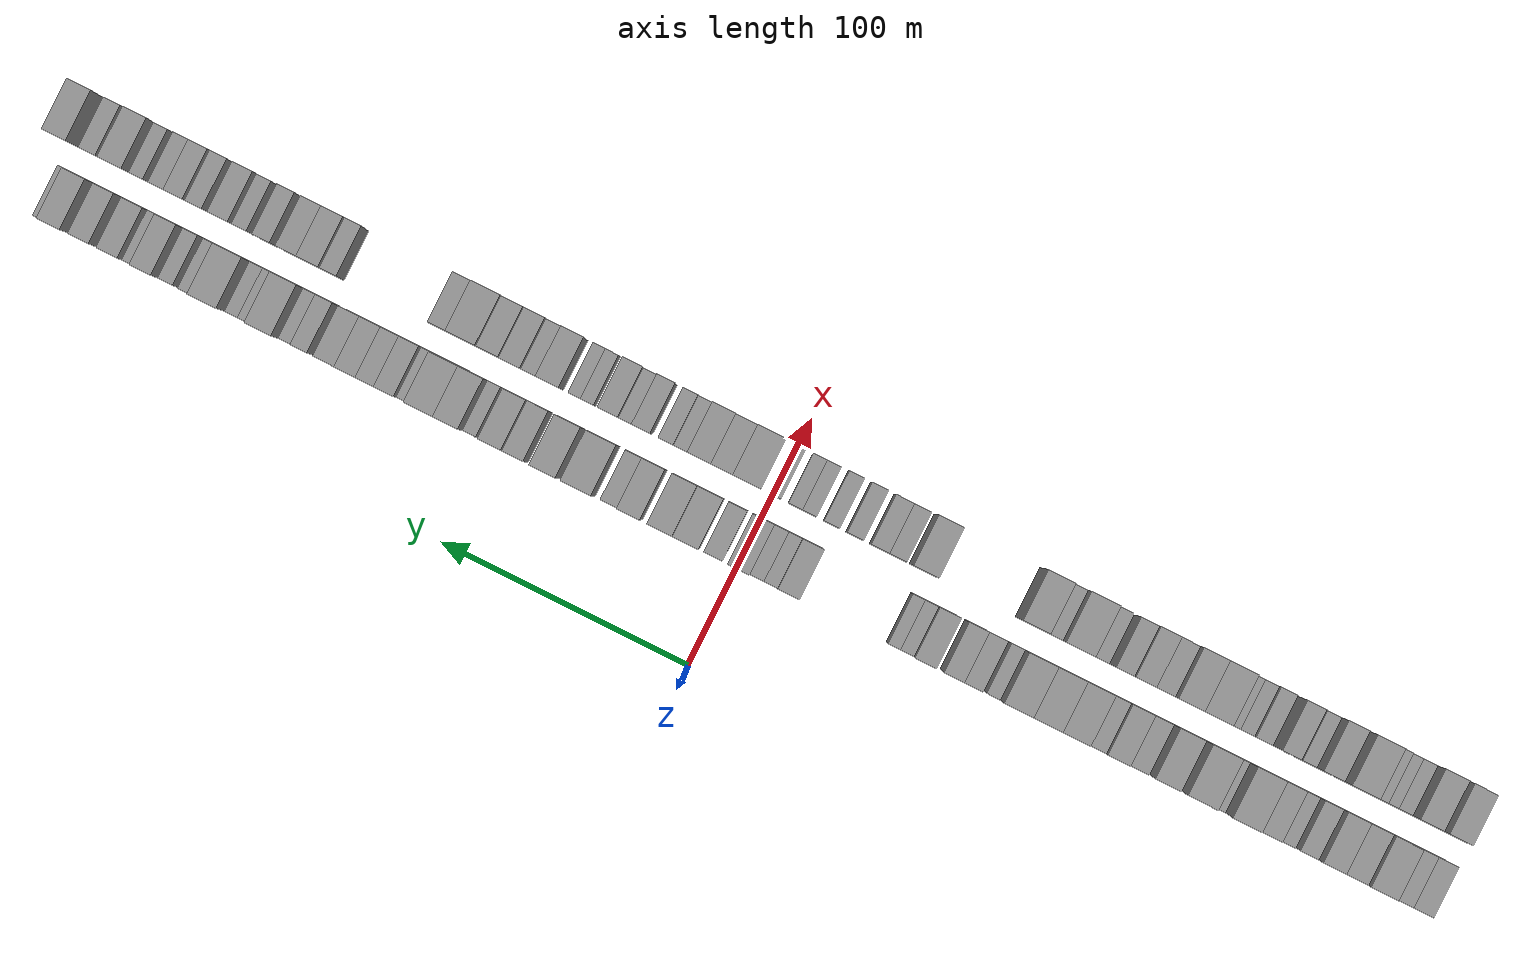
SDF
<sdf version="1.6">
 <world name="default">
  <scene>
   <sky><clouds><speed>12</speed></clouds></sky>
   <ambient>0.4 0.4 0.4 1</ambient>
   <background>0.7 0.7 0.7 1</background>
   <shadows>1</shadows>
  </scene>
  <gravity>0 0 -9.8066</gravity>
  <magnetic_field>6e-06 2.3e-05 -4.2e-05</magnetic_field>
  <physics default="0" name="default_physics" type="ode">
   <ode>
    <solver>
     <type>quick</type>
     <iters>10</iters>
     <sor>1.0</sor>
     <use_dynamic_moi_rescaling>0</use_dynamic_moi_rescaling>
    </solver>
    <constraints>
     <cfm>0</cfm>
     <erp>0.2</erp>
     <contact_max_correcting_vel>100</contact_max_correcting_vel>
     <contact_surface_layer>0.001</contact_surface_layer>
    </constraints>
   </ode>
   <max_step_size>0.004</max_step_size>
   <real_time_factor>1</real_time_factor>
   <real_time_update_rate>250</real_time_update_rate>
  </physics>
  <light name="sun" type="directional">
   <pose>0 0 10 0 0 0</pose>
   <diffuse>0.8 0.8 0.8 1</diffuse>
   <specular>0.2 0.2 0.2 1</specular>
   <attenuation>
    <range>1000</range>
    <constant>0.9</constant>
    <linear>0.01</linear>
    <quadratic>0.001</quadratic>
   </attenuation>
   <direction>-0.5 0.1 -0.9</direction>
  </light>
  <model name="building_1">
   <static>1</static>
   <pose>50.0000 -272.0312 0 0.000000 0.000000 0.000000</pose>
   <link name="link">
    <pose>0 0 9.00 0 0 0</pose>
    <collision name="collision"><geometry><box><size>20.0000 7.9376 18.0000</size></box></geometry></collision>
    <visual name="visual">
     <cast_shadows>0</cast_shadows>
     <geometry><box><size>20.0000 7.9376 18.0000</size></box></geometry>
     <material>
      <script>
       <uri>model://grey_wall/materials/scripts</uri>
       <uri>model://grey_wall/materials/textures</uri>
       <name>vrc/grey_wall</name>
      </script>
     </material>
    </visual>
   </link>
  </model>
  <model name="building_2">
   <static>1</static>
   <pose>50.0000 -264.0821 0 0.000000 0.000000 0.000000</pose>
   <link name="link">
    <pose>0 0 9.00 0 0 0</pose>
    <collision name="collision"><geometry><box><size>20.0000 7.9607 18.0000</size></box></geometry></collision>
    <visual name="visual">
     <cast_shadows>0</cast_shadows>
     <geometry><box><size>20.0000 7.9607 18.0000</size></box></geometry>
     <material>
      <script>
       <uri>model://grey_wall/materials/scripts</uri>
       <uri>model://grey_wall/materials/textures</uri>
       <name>vrc/grey_wall</name>
      </script>
     </material>
    </visual>
   </link>
  </model>
  <model name="building_3">
   <static>1</static>
   <pose>50.0000 -254.6737 0 0.000000 0.000000 0.000000</pose>
   <link name="link">
    <pose>0 0 12.00 0 0 0</pose>
    <collision name="collision"><geometry><box><size>20.0000 10.8561 24.0000</size></box></geometry></collision>
    <visual name="visual">
     <cast_shadows>0</cast_shadows>
     <geometry><box><size>20.0000 10.8561 24.0000</size></box></geometry>
     <material>
      <script>
       <uri>model://grey_wall/materials/scripts</uri>
       <uri>model://grey_wall/materials/textures</uri>
       <name>vrc/grey_wall</name>
      </script>
     </material>
    </visual>
   </link>
  </model>
  <model name="building_4">
   <static>1</static>
   <pose>50.0000 -244.8792 0 0.000000 0.000000 0.000000</pose>
   <link name="link">
    <pose>0 0 10.50 0 0 0</pose>
    <collision name="collision"><geometry><box><size>20.0000 8.7328 21.0000</size></box></geometry></collision>
    <visual name="visual">
     <cast_shadows>0</cast_shadows>
     <geometry><box><size>20.0000 8.7328 21.0000</size></box></geometry>
     <material>
      <script>
       <uri>model://grey_wall/materials/scripts</uri>
       <uri>model://grey_wall/materials/textures</uri>
       <name>vrc/grey_wall</name>
      </script>
     </material>
    </visual>
   </link>
  </model>
  <model name="building_5">
   <static>1</static>
   <pose>50.0000 -235.9387 0 0.000000 0.000000 0.000000</pose>
   <link name="link">
    <pose>0 0 10.50 0 0 0</pose>
    <collision name="collision"><geometry><box><size>20.0000 9.1483 21.0000</size></box></geometry></collision>
    <visual name="visual">
     <cast_shadows>0</cast_shadows>
     <geometry><box><size>20.0000 9.1483 21.0000</size></box></geometry>
     <material>
      <script>
       <uri>model://grey_wall/materials/scripts</uri>
       <uri>model://grey_wall/materials/textures</uri>
       <name>vrc/grey_wall</name>
      </script>
     </material>
    </visual>
   </link>
  </model>
  <model name="building_6">
   <static>1</static>
   <pose>50.0000 -227.6828 0 0.000000 0.000000 0.000000</pose>
   <link name="link">
    <pose>0 0 7.50 0 0 0</pose>
    <collision name="collision"><geometry><box><size>20.0000 7.3636 15.0000</size></box></geometry></collision>
    <visual name="visual">
     <cast_shadows>0</cast_shadows>
     <geometry><box><size>20.0000 7.3636 15.0000</size></box></geometry>
     <material>
      <script>
       <uri>model://grey_wall/materials/scripts</uri>
       <uri>model://grey_wall/materials/textures</uri>
       <name>vrc/grey_wall</name>
      </script>
     </material>
    </visual>
   </link>
  </model>
  <model name="building_7">
   <static>1</static>
   <pose>50.0000 -218.6321 0 0.000000 0.000000 0.000000</pose>
   <link name="link">
    <pose>0 0 7.50 0 0 0</pose>
    <collision name="collision"><geometry><box><size>20.0000 6.7378 15.0000</size></box></geometry></collision>
    <visual name="visual">
     <cast_shadows>0</cast_shadows>
     <geometry><box><size>20.0000 6.7378 15.0000</size></box></geometry>
     <material>
      <script>
       <uri>model://grey_wall/materials/scripts</uri>
       <uri>model://grey_wall/materials/textures</uri>
       <name>vrc/grey_wall</name>
      </script>
     </material>
    </visual>
   </link>
  </model>
  <model name="building_8">
   <static>1</static>
   <pose>50.0000 -210.8865 0 0.000000 0.000000 0.000000</pose>
   <link name="link">
    <pose>0 0 10.50 0 0 0</pose>
    <collision name="collision"><geometry><box><size>20.0000 8.7534 21.0000</size></box></geometry></collision>
    <visual name="visual">
     <cast_shadows>0</cast_shadows>
     <geometry><box><size>20.0000 8.7534 21.0000</size></box></geometry>
     <material>
      <script>
       <uri>model://grey_wall/materials/scripts</uri>
       <uri>model://grey_wall/materials/textures</uri>
       <name>vrc/grey_wall</name>
      </script>
     </material>
    </visual>
   </link>
  </model>
  <model name="building_9">
   <static>1</static>
   <pose>50.0000 -200.6909 0 0.000000 0.000000 0.000000</pose>
   <link name="link">
    <pose>0 0 12.00 0 0 0</pose>
    <collision name="collision"><geometry><box><size>20.0000 11.6380 24.0000</size></box></geometry></collision>
    <visual name="visual">
     <cast_shadows>0</cast_shadows>
     <geometry><box><size>20.0000 11.6380 24.0000</size></box></geometry>
     <material>
      <script>
       <uri>model://grey_wall/materials/scripts</uri>
       <uri>model://grey_wall/materials/textures</uri>
       <name>vrc/grey_wall</name>
      </script>
     </material>
    </visual>
   </link>
  </model>
  <model name="building_10">
   <static>1</static>
   <pose>50.0000 -192.0684 0 0.000000 0.000000 0.000000</pose>
   <link name="link">
    <pose>0 0 6.00 0 0 0</pose>
    <collision name="collision"><geometry><box><size>20.0000 5.6070 12.0000</size></box></geometry></collision>
    <visual name="visual">
     <cast_shadows>0</cast_shadows>
     <geometry><box><size>20.0000 5.6070 12.0000</size></box></geometry>
     <material>
      <script>
       <uri>model://grey_wall/materials/scripts</uri>
       <uri>model://grey_wall/materials/textures</uri>
       <name>vrc/grey_wall</name>
      </script>
     </material>
    </visual>
   </link>
  </model>
  <model name="building_11">
   <static>1</static>
   <pose>50.0000 -183.3076 0 0.000000 0.000000 0.000000</pose>
   <link name="link">
    <pose>0 0 12.00 0 0 0</pose>
    <collision name="collision"><geometry><box><size>20.0000 11.9145 24.0000</size></box></geometry></collision>
    <visual name="visual">
     <cast_shadows>0</cast_shadows>
     <geometry><box><size>20.0000 11.9145 24.0000</size></box></geometry>
     <material>
      <script>
       <uri>model://grey_wall/materials/scripts</uri>
       <uri>model://grey_wall/materials/textures</uri>
       <name>vrc/grey_wall</name>
      </script>
     </material>
    </visual>
   </link>
  </model>
  <model name="building_12">
   <static>1</static>
   <pose>50.0000 -170.2685 0 0.000000 0.000000 0.000000</pose>
   <link name="link">
    <pose>0 0 10.50 0 0 0</pose>
    <collision name="collision"><geometry><box><size>20.0000 10.1637 21.0000</size></box></geometry></collision>
    <visual name="visual">
     <cast_shadows>0</cast_shadows>
     <geometry><box><size>20.0000 10.1637 21.0000</size></box></geometry>
     <material>
      <script>
       <uri>model://grey_wall/materials/scripts</uri>
       <uri>model://grey_wall/materials/textures</uri>
       <name>vrc/grey_wall</name>
      </script>
     </material>
    </visual>
   </link>
  </model>
  <model name="building_13">
   <static>1</static>
   <pose>50.0000 -159.2767 0 0.000000 0.000000 0.000000</pose>
   <link name="link">
    <pose>0 0 9.00 0 0 0</pose>
    <collision name="collision"><geometry><box><size>20.0000 7.8200 18.0000</size></box></geometry></collision>
    <visual name="visual">
     <cast_shadows>0</cast_shadows>
     <geometry><box><size>20.0000 7.8200 18.0000</size></box></geometry>
     <material>
      <script>
       <uri>model://grey_wall/materials/scripts</uri>
       <uri>model://grey_wall/materials/textures</uri>
       <name>vrc/grey_wall</name>
      </script>
     </material>
    </visual>
   </link>
  </model>
  <model name="building_14">
   <static>1</static>
   <pose>50.0000 -150.8688 0 0.000000 0.000000 0.000000</pose>
   <link name="link">
    <pose>0 0 10.50 0 0 0</pose>
    <collision name="collision"><geometry><box><size>20.0000 8.9957 21.0000</size></box></geometry></collision>
    <visual name="visual">
     <cast_shadows>0</cast_shadows>
     <geometry><box><size>20.0000 8.9957 21.0000</size></box></geometry>
     <material>
      <script>
       <uri>model://grey_wall/materials/scripts</uri>
       <uri>model://grey_wall/materials/textures</uri>
       <name>vrc/grey_wall</name>
      </script>
     </material>
    </visual>
   </link>
  </model>
  <model name="building_15">
   <static>1</static>
   <pose>50.0000 -142.7405 0 0.000000 0.000000 0.000000</pose>
   <link name="link">
    <pose>0 0 9.00 0 0 0</pose>
    <collision name="collision"><geometry><box><size>20.0000 7.2610 18.0000</size></box></geometry></collision>
    <visual name="visual">
     <cast_shadows>0</cast_shadows>
     <geometry><box><size>20.0000 7.2610 18.0000</size></box></geometry>
     <material>
      <script>
       <uri>model://grey_wall/materials/scripts</uri>
       <uri>model://grey_wall/materials/textures</uri>
       <name>vrc/grey_wall</name>
      </script>
     </material>
    </visual>
   </link>
  </model>
  <model name="building_16">
   <static>1</static>
   <pose>50.0000 -133.6735 0 0.000000 0.000000 0.000000</pose>
   <link name="link">
    <pose>0 0 12.00 0 0 0</pose>
    <collision name="collision"><geometry><box><size>20.0000 10.8730 24.0000</size></box></geometry></collision>
    <visual name="visual">
     <cast_shadows>0</cast_shadows>
     <geometry><box><size>20.0000 10.8730 24.0000</size></box></geometry>
     <material>
      <script>
       <uri>model://grey_wall/materials/scripts</uri>
       <uri>model://grey_wall/materials/textures</uri>
       <name>vrc/grey_wall</name>
      </script>
     </material>
    </visual>
   </link>
  </model>
  <model name="building_17">
   <static>1</static>
   <pose>50.0000 -122.4507 0 0.000000 0.000000 0.000000</pose>
   <link name="link">
    <pose>0 0 12.00 0 0 0</pose>
    <collision name="collision"><geometry><box><size>20.0000 11.5726 24.0000</size></box></geometry></collision>
    <visual name="visual">
     <cast_shadows>0</cast_shadows>
     <geometry><box><size>20.0000 11.5726 24.0000</size></box></geometry>
     <material>
      <script>
       <uri>model://grey_wall/materials/scripts</uri>
       <uri>model://grey_wall/materials/textures</uri>
       <name>vrc/grey_wall</name>
      </script>
     </material>
    </visual>
   </link>
  </model>
  <model name="building_18">
   <static>1</static>
   <pose>50.0000 -110.8684 0 0.000000 0.000000 0.000000</pose>
   <link name="link">
    <pose>0 0 12.00 0 0 0</pose>
    <collision name="collision"><geometry><box><size>20.0000 11.5920 24.0000</size></box></geometry></collision>
    <visual name="visual">
     <cast_shadows>0</cast_shadows>
     <geometry><box><size>20.0000 11.5920 24.0000</size></box></geometry>
     <material>
      <script>
       <uri>model://grey_wall/materials/scripts</uri>
       <uri>model://grey_wall/materials/textures</uri>
       <name>vrc/grey_wall</name>
      </script>
     </material>
    </visual>
   </link>
  </model>
  <model name="building_19">
   <static>1</static>
   <pose>50.0000 -102.3278 0 0.000000 0.000000 0.000000</pose>
   <link name="link">
    <pose>0 0 6.00 0 0 0</pose>
    <collision name="collision"><geometry><box><size>20.0000 5.4891 12.0000</size></box></geometry></collision>
    <visual name="visual">
     <cast_shadows>0</cast_shadows>
     <geometry><box><size>20.0000 5.4891 12.0000</size></box></geometry>
     <material>
      <script>
       <uri>model://grey_wall/materials/scripts</uri>
       <uri>model://grey_wall/materials/textures</uri>
       <name>vrc/grey_wall</name>
      </script>
     </material>
    </visual>
   </link>
  </model>
  <model name="building_20">
   <static>1</static>
   <pose>50.0000 -93.8886 0 0.000000 0.000000 0.000000</pose>
   <link name="link">
    <pose>0 0 9.00 0 0 0</pose>
    <collision name="collision"><geometry><box><size>20.0000 7.3894 18.0000</size></box></geometry></collision>
    <visual name="visual">
     <cast_shadows>0</cast_shadows>
     <geometry><box><size>20.0000 7.3894 18.0000</size></box></geometry>
     <material>
      <script>
       <uri>model://grey_wall/materials/scripts</uri>
       <uri>model://grey_wall/materials/textures</uri>
       <name>vrc/grey_wall</name>
      </script>
     </material>
    </visual>
   </link>
  </model>
  <model name="building_21">
   <static>1</static>
   <pose>50.0000 -86.1221 0 0.000000 0.000000 0.000000</pose>
   <link name="link">
    <pose>0 0 9.00 0 0 0</pose>
    <collision name="collision"><geometry><box><size>20.0000 8.1436 18.0000</size></box></geometry></collision>
    <visual name="visual">
     <cast_shadows>0</cast_shadows>
     <geometry><box><size>20.0000 8.1436 18.0000</size></box></geometry>
     <material>
      <script>
       <uri>model://grey_wall/materials/scripts</uri>
       <uri>model://grey_wall/materials/textures</uri>
       <name>vrc/grey_wall</name>
      </script>
     </material>
    </visual>
   </link>
  </model>
  <model name="building_22">
   <static>1</static>
   <pose>50.0000 -74.8031 0 0.000000 0.000000 0.000000</pose>
   <link name="link">
    <pose>0 0 9.00 0 0 0</pose>
    <collision name="collision"><geometry><box><size>20.0000 8.4944 18.0000</size></box></geometry></collision>
    <visual name="visual">
     <cast_shadows>0</cast_shadows>
     <geometry><box><size>20.0000 8.4944 18.0000</size></box></geometry>
     <material>
      <script>
       <uri>model://grey_wall/materials/scripts</uri>
       <uri>model://grey_wall/materials/textures</uri>
       <name>vrc/grey_wall</name>
      </script>
     </material>
    </visual>
   </link>
  </model>
  <model name="building_23">
   <static>1</static>
   <pose>50.0000 -67.8921 0 0.000000 0.000000 0.000000</pose>
   <link name="link">
    <pose>0 0 6.00 0 0 0</pose>
    <collision name="collision"><geometry><box><size>20.0000 5.3276 12.0000</size></box></geometry></collision>
    <visual name="visual">
     <cast_shadows>0</cast_shadows>
     <geometry><box><size>20.0000 5.3276 12.0000</size></box></geometry>
     <material>
      <script>
       <uri>model://grey_wall/materials/scripts</uri>
       <uri>model://grey_wall/materials/textures</uri>
       <name>vrc/grey_wall</name>
      </script>
     </material>
    </visual>
   </link>
  </model>
  <model name="building_24">
   <static>1</static>
   <pose>50.0000 -62.7236 0 0.000000 0.000000 0.000000</pose>
   <link name="link">
    <pose>0 0 6.00 0 0 0</pose>
    <collision name="collision"><geometry><box><size>20.0000 5.0095 12.0000</size></box></geometry></collision>
    <visual name="visual">
     <cast_shadows>0</cast_shadows>
     <geometry><box><size>20.0000 5.0095 12.0000</size></box></geometry>
     <material>
      <script>
       <uri>model://grey_wall/materials/scripts</uri>
       <uri>model://grey_wall/materials/textures</uri>
       <name>vrc/grey_wall</name>
      </script>
     </material>
    </visual>
   </link>
  </model>
  <model name="building_25">
   <static>1</static>
   <pose>50.0000 -20.4532 0 0.000000 0.000000 0.000000</pose>
   <link name="link">
    <pose>0 0 9.00 0 0 0</pose>
    <collision name="collision"><geometry><box><size>20.0000 8.5104 18.0000</size></box></geometry></collision>
    <visual name="visual">
     <cast_shadows>0</cast_shadows>
     <geometry><box><size>20.0000 8.5104 18.0000</size></box></geometry>
     <material>
      <script>
       <uri>model://grey_wall/materials/scripts</uri>
       <uri>model://grey_wall/materials/textures</uri>
       <name>vrc/grey_wall</name>
      </script>
     </material>
    </visual>
   </link>
  </model>
  <model name="building_26">
   <static>1</static>
   <pose>50.0000 -13.4465 0 0.000000 0.000000 0.000000</pose>
   <link name="link">
    <pose>0 0 6.00 0 0 0</pose>
    <collision name="collision"><geometry><box><size>20.0000 5.5029 12.0000</size></box></geometry></collision>
    <visual name="visual">
     <cast_shadows>0</cast_shadows>
     <geometry><box><size>20.0000 5.5029 12.0000</size></box></geometry>
     <material>
      <script>
       <uri>model://grey_wall/materials/scripts</uri>
       <uri>model://grey_wall/materials/textures</uri>
       <name>vrc/grey_wall</name>
      </script>
     </material>
    </visual>
   </link>
  </model>
  <model name="building_27">
   <static>1</static>
   <pose>50.0000 -7.8322 0 0.000000 0.000000 0.000000</pose>
   <link name="link">
    <pose>0 0 6.00 0 0 0</pose>
    <collision name="collision"><geometry><box><size>20.0000 5.7257 12.0000</size></box></geometry></collision>
    <visual name="visual">
     <cast_shadows>0</cast_shadows>
     <geometry><box><size>20.0000 5.7257 12.0000</size></box></geometry>
     <material>
      <script>
       <uri>model://grey_wall/materials/scripts</uri>
       <uri>model://grey_wall/materials/textures</uri>
       <name>vrc/grey_wall</name>
      </script>
     </material>
    </visual>
   </link>
  </model>
  <model name="building_28">
   <static>1</static>
   <pose>50.0000 -0.5983 0 0.000000 0.000000 0.000000</pose>
   <link name="link">
    <pose>0 0 10.50 0 0 0</pose>
    <collision name="collision"><geometry><box><size>20.0000 8.7422 21.0000</size></box></geometry></collision>
    <visual name="visual">
     <cast_shadows>0</cast_shadows>
     <geometry><box><size>20.0000 8.7422 21.0000</size></box></geometry>
     <material>
      <script>
       <uri>model://grey_wall/materials/scripts</uri>
       <uri>model://grey_wall/materials/textures</uri>
       <name>vrc/grey_wall</name>
      </script>
     </material>
    </visual>
   </link>
  </model>
  <model name="building_29">
   <static>1</static>
   <pose>50.0000 9.5227 0 0.000000 0.000000 0.000000</pose>
   <link name="link">
    <pose>0 0 7.50 0 0 0</pose>
    <collision name="collision"><geometry><box><size>20.0000 7.4998 15.0000</size></box></geometry></collision>
    <visual name="visual">
     <cast_shadows>0</cast_shadows>
     <geometry><box><size>20.0000 7.4998 15.0000</size></box></geometry>
     <material>
      <script>
       <uri>model://grey_wall/materials/scripts</uri>
       <uri>model://grey_wall/materials/textures</uri>
       <name>vrc/grey_wall</name>
      </script>
     </material>
    </visual>
   </link>
  </model>
  <model name="building_30">
   <static>1</static>
   <pose>50.0000 20.4144 0 0.000000 0.000000 0.000000</pose>
   <link name="link">
    <pose>0 0 10.50 0 0 0</pose>
    <collision name="collision"><geometry><box><size>20.0000 10.2836 21.0000</size></box></geometry></collision>
    <visual name="visual">
     <cast_shadows>0</cast_shadows>
     <geometry><box><size>20.0000 10.2836 21.0000</size></box></geometry>
     <material>
      <script>
       <uri>model://grey_wall/materials/scripts</uri>
       <uri>model://grey_wall/materials/textures</uri>
       <name>vrc/grey_wall</name>
      </script>
     </material>
    </visual>
   </link>
  </model>
  <model name="building_31">
   <static>1</static>
   <pose>50.0000 30.5197 0 0.000000 0.000000 0.000000</pose>
   <link name="link">
    <pose>0 0 12.00 0 0 0</pose>
    <collision name="collision"><geometry><box><size>20.0000 9.9270 24.0000</size></box></geometry></collision>
    <visual name="visual">
     <cast_shadows>0</cast_shadows>
     <geometry><box><size>20.0000 9.9270 24.0000</size></box></geometry>
     <material>
      <script>
       <uri>model://grey_wall/materials/scripts</uri>
       <uri>model://grey_wall/materials/textures</uri>
       <name>vrc/grey_wall</name>
      </script>
     </material>
    </visual>
   </link>
  </model>
  <model name="building_32">
   <static>1</static>
   <pose>50.0000 43.0216 0 0.000000 0.000000 0.000000</pose>
   <link name="link">
    <pose>0 0 10.50 0 0 0</pose>
    <collision name="collision"><geometry><box><size>20.0000 9.0767 21.0000</size></box></geometry></collision>
    <visual name="visual">
     <cast_shadows>0</cast_shadows>
     <geometry><box><size>20.0000 9.0767 21.0000</size></box></geometry>
     <material>
      <script>
       <uri>model://grey_wall/materials/scripts</uri>
       <uri>model://grey_wall/materials/textures</uri>
       <name>vrc/grey_wall</name>
      </script>
     </material>
    </visual>
   </link>
  </model>
  <model name="building_33">
   <static>1</static>
   <pose>50.0000 51.0363 0 0.000000 0.000000 0.000000</pose>
   <link name="link">
    <pose>0 0 7.50 0 0 0</pose>
    <collision name="collision"><geometry><box><size>20.0000 6.9528 15.0000</size></box></geometry></collision>
    <visual name="visual">
     <cast_shadows>0</cast_shadows>
     <geometry><box><size>20.0000 6.9528 15.0000</size></box></geometry>
     <material>
      <script>
       <uri>model://grey_wall/materials/scripts</uri>
       <uri>model://grey_wall/materials/textures</uri>
       <name>vrc/grey_wall</name>
      </script>
     </material>
    </visual>
   </link>
  </model>
  <model name="building_34">
   <static>1</static>
   <pose>50.0000 63.4935 0 0.000000 0.000000 0.000000</pose>
   <link name="link">
    <pose>0 0 12.00 0 0 0</pose>
    <collision name="collision"><geometry><box><size>20.0000 11.9616 24.0000</size></box></geometry></collision>
    <visual name="visual">
     <cast_shadows>0</cast_shadows>
     <geometry><box><size>20.0000 11.9616 24.0000</size></box></geometry>
     <material>
      <script>
       <uri>model://grey_wall/materials/scripts</uri>
       <uri>model://grey_wall/materials/textures</uri>
       <name>vrc/grey_wall</name>
      </script>
     </material>
    </visual>
   </link>
  </model>
  <model name="building_35">
   <static>1</static>
   <pose>50.0000 76.6014 0 0.000000 0.000000 0.000000</pose>
   <link name="link">
    <pose>0 0 12.00 0 0 0</pose>
    <collision name="collision"><geometry><box><size>20.0000 10.2541 24.0000</size></box></geometry></collision>
    <visual name="visual">
     <cast_shadows>0</cast_shadows>
     <geometry><box><size>20.0000 10.2541 24.0000</size></box></geometry>
     <material>
      <script>
       <uri>model://grey_wall/materials/scripts</uri>
       <uri>model://grey_wall/materials/textures</uri>
       <name>vrc/grey_wall</name>
      </script>
     </material>
    </visual>
   </link>
  </model>
  <model name="building_36">
   <static>1</static>
   <pose>50.0000 88.9889 0 0.000000 0.000000 0.000000</pose>
   <link name="link">
    <pose>0 0 9.00 0 0 0</pose>
    <collision name="collision"><geometry><box><size>20.0000 8.5208 18.0000</size></box></geometry></collision>
    <visual name="visual">
     <cast_shadows>0</cast_shadows>
     <geometry><box><size>20.0000 8.5208 18.0000</size></box></geometry>
     <material>
      <script>
       <uri>model://grey_wall/materials/scripts</uri>
       <uri>model://grey_wall/materials/textures</uri>
       <name>vrc/grey_wall</name>
      </script>
     </material>
    </visual>
   </link>
  </model>
  <model name="building_37">
   <static>1</static>
   <pose>50.0000 97.8309 0 0.000000 0.000000 0.000000</pose>
   <link name="link">
    <pose>0 0 10.50 0 0 0</pose>
    <collision name="collision"><geometry><box><size>20.0000 9.1632 21.0000</size></box></geometry></collision>
    <visual name="visual">
     <cast_shadows>0</cast_shadows>
     <geometry><box><size>20.0000 9.1632 21.0000</size></box></geometry>
     <material>
      <script>
       <uri>model://grey_wall/materials/scripts</uri>
       <uri>model://grey_wall/materials/textures</uri>
       <name>vrc/grey_wall</name>
      </script>
     </material>
    </visual>
   </link>
  </model>
  <model name="building_38">
   <static>1</static>
   <pose>50.0000 107.0473 0 0.000000 0.000000 0.000000</pose>
   <link name="link">
    <pose>0 0 6.00 0 0 0</pose>
    <collision name="collision"><geometry><box><size>20.0000 5.2696 12.0000</size></box></geometry></collision>
    <visual name="visual">
     <cast_shadows>0</cast_shadows>
     <geometry><box><size>20.0000 5.2696 12.0000</size></box></geometry>
     <material>
      <script>
       <uri>model://grey_wall/materials/scripts</uri>
       <uri>model://grey_wall/materials/textures</uri>
       <name>vrc/grey_wall</name>
      </script>
     </material>
    </visual>
   </link>
  </model>
  <model name="building_39">
   <static>1</static>
   <pose>50.0000 114.6969 0 0.000000 0.000000 0.000000</pose>
   <link name="link">
    <pose>0 0 12.00 0 0 0</pose>
    <collision name="collision"><geometry><box><size>20.0000 10.0296 24.0000</size></box></geometry></collision>
    <visual name="visual">
     <cast_shadows>0</cast_shadows>
     <geometry><box><size>20.0000 10.0296 24.0000</size></box></geometry>
     <material>
      <script>
       <uri>model://grey_wall/materials/scripts</uri>
       <uri>model://grey_wall/materials/textures</uri>
       <name>vrc/grey_wall</name>
      </script>
     </material>
    </visual>
   </link>
  </model>
  <model name="building_40">
   <static>1</static>
   <pose>50.0000 125.4278 0 0.000000 0.000000 0.000000</pose>
   <link name="link">
    <pose>0 0 12.00 0 0 0</pose>
    <collision name="collision"><geometry><box><size>20.0000 11.4323 24.0000</size></box></geometry></collision>
    <visual name="visual">
     <cast_shadows>0</cast_shadows>
     <geometry><box><size>20.0000 11.4323 24.0000</size></box></geometry>
     <material>
      <script>
       <uri>model://grey_wall/materials/scripts</uri>
       <uri>model://grey_wall/materials/textures</uri>
       <name>vrc/grey_wall</name>
      </script>
     </material>
    </visual>
   </link>
  </model>
  <model name="building_41">
   <static>1</static>
   <pose>50.0000 133.6184 0 0.000000 0.000000 0.000000</pose>
   <link name="link">
    <pose>0 0 6.00 0 0 0</pose>
    <collision name="collision"><geometry><box><size>20.0000 4.9488 12.0000</size></box></geometry></collision>
    <visual name="visual">
     <cast_shadows>0</cast_shadows>
     <geometry><box><size>20.0000 4.9488 12.0000</size></box></geometry>
     <material>
      <script>
       <uri>model://grey_wall/materials/scripts</uri>
       <uri>model://grey_wall/materials/textures</uri>
       <name>vrc/grey_wall</name>
      </script>
     </material>
    </visual>
   </link>
  </model>
  <model name="building_42">
   <static>1</static>
   <pose>50.0000 140.0603 0 0.000000 0.000000 0.000000</pose>
   <link name="link">
    <pose>0 0 9.00 0 0 0</pose>
    <collision name="collision"><geometry><box><size>20.0000 7.9351 18.0000</size></box></geometry></collision>
    <visual name="visual">
     <cast_shadows>0</cast_shadows>
     <geometry><box><size>20.0000 7.9351 18.0000</size></box></geometry>
     <material>
      <script>
       <uri>model://grey_wall/materials/scripts</uri>
       <uri>model://grey_wall/materials/textures</uri>
       <name>vrc/grey_wall</name>
      </script>
     </material>
    </visual>
   </link>
  </model>
  <model name="building_43">
   <static>1</static>
   <pose>50.0000 147.6776 0 0.000000 0.000000 0.000000</pose>
   <link name="link">
    <pose>0 0 9.00 0 0 0</pose>
    <collision name="collision"><geometry><box><size>20.0000 7.2995 18.0000</size></box></geometry></collision>
    <visual name="visual">
     <cast_shadows>0</cast_shadows>
     <geometry><box><size>20.0000 7.2995 18.0000</size></box></geometry>
     <material>
      <script>
       <uri>model://grey_wall/materials/scripts</uri>
       <uri>model://grey_wall/materials/textures</uri>
       <name>vrc/grey_wall</name>
      </script>
     </material>
    </visual>
   </link>
  </model>
  <model name="building_44">
   <static>1</static>
   <pose>50.0000 155.5163 0 0.000000 0.000000 0.000000</pose>
   <link name="link">
    <pose>0 0 9.00 0 0 0</pose>
    <collision name="collision"><geometry><box><size>20.0000 8.3779 18.0000</size></box></geometry></collision>
    <visual name="visual">
     <cast_shadows>0</cast_shadows>
     <geometry><box><size>20.0000 8.3779 18.0000</size></box></geometry>
     <material>
      <script>
       <uri>model://grey_wall/materials/scripts</uri>
       <uri>model://grey_wall/materials/textures</uri>
       <name>vrc/grey_wall</name>
      </script>
     </material>
    </visual>
   </link>
  </model>
  <model name="building_45">
   <static>1</static>
   <pose>50.0000 163.8533 0 0.000000 0.000000 0.000000</pose>
   <link name="link">
    <pose>0 0 9.00 0 0 0</pose>
    <collision name="collision"><geometry><box><size>20.0000 8.2960 18.0000</size></box></geometry></collision>
    <visual name="visual">
     <cast_shadows>0</cast_shadows>
     <geometry><box><size>20.0000 8.2960 18.0000</size></box></geometry>
     <material>
      <script>
       <uri>model://grey_wall/materials/scripts</uri>
       <uri>model://grey_wall/materials/textures</uri>
       <name>vrc/grey_wall</name>
      </script>
     </material>
    </visual>
   </link>
  </model>
  <model name="building_46">
   <static>1</static>
   <pose>50.0000 174.3933 0 0.000000 0.000000 0.000000</pose>
   <link name="link">
    <pose>0 0 7.50 0 0 0</pose>
    <collision name="collision"><geometry><box><size>20.0000 6.7841 15.0000</size></box></geometry></collision>
    <visual name="visual">
     <cast_shadows>0</cast_shadows>
     <geometry><box><size>20.0000 6.7841 15.0000</size></box></geometry>
     <material>
      <script>
       <uri>model://grey_wall/materials/scripts</uri>
       <uri>model://grey_wall/materials/textures</uri>
       <name>vrc/grey_wall</name>
      </script>
     </material>
    </visual>
   </link>
  </model>
  <model name="building_47">
   <static>1</static>
   <pose>50.0000 180.4673 0 0.000000 0.000000 0.000000</pose>
   <link name="link">
    <pose>0 0 6.00 0 0 0</pose>
    <collision name="collision"><geometry><box><size>20.0000 5.3639 12.0000</size></box></geometry></collision>
    <visual name="visual">
     <cast_shadows>0</cast_shadows>
     <geometry><box><size>20.0000 5.3639 12.0000</size></box></geometry>
     <material>
      <script>
       <uri>model://grey_wall/materials/scripts</uri>
       <uri>model://grey_wall/materials/textures</uri>
       <name>vrc/grey_wall</name>
      </script>
     </material>
    </visual>
   </link>
  </model>
  <model name="building_48">
   <static>1</static>
   <pose>50.0000 188.4037 0 0.000000 0.000000 0.000000</pose>
   <link name="link">
    <pose>0 0 12.00 0 0 0</pose>
    <collision name="collision"><geometry><box><size>20.0000 10.5089 24.0000</size></box></geometry></collision>
    <visual name="visual">
     <cast_shadows>0</cast_shadows>
     <geometry><box><size>20.0000 10.5089 24.0000</size></box></geometry>
     <material>
      <script>
       <uri>model://grey_wall/materials/scripts</uri>
       <uri>model://grey_wall/materials/textures</uri>
       <name>vrc/grey_wall</name>
      </script>
     </material>
    </visual>
   </link>
  </model>
  <model name="building_49">
   <static>1</static>
   <pose>50.0000 196.5371 0 0.000000 0.000000 0.000000</pose>
   <link name="link">
    <pose>0 0 6.00 0 0 0</pose>
    <collision name="collision"><geometry><box><size>20.0000 5.7578 12.0000</size></box></geometry></collision>
    <visual name="visual">
     <cast_shadows>0</cast_shadows>
     <geometry><box><size>20.0000 5.7578 12.0000</size></box></geometry>
     <material>
      <script>
       <uri>model://grey_wall/materials/scripts</uri>
       <uri>model://grey_wall/materials/textures</uri>
       <name>vrc/grey_wall</name>
      </script>
     </material>
    </visual>
   </link>
  </model>
  <model name="building_50">
   <static>1</static>
   <pose>50.0000 202.0249 0 0.000000 0.000000 0.000000</pose>
   <link name="link">
    <pose>0 0 6.00 0 0 0</pose>
    <collision name="collision"><geometry><box><size>20.0000 5.2178 12.0000</size></box></geometry></collision>
    <visual name="visual">
     <cast_shadows>0</cast_shadows>
     <geometry><box><size>20.0000 5.2178 12.0000</size></box></geometry>
     <material>
      <script>
       <uri>model://grey_wall/materials/scripts</uri>
       <uri>model://grey_wall/materials/textures</uri>
       <name>vrc/grey_wall</name>
      </script>
     </material>
    </visual>
   </link>
  </model>
  <model name="building_51">
   <static>1</static>
   <pose>50.0000 210.3792 0 0.000000 0.000000 0.000000</pose>
   <link name="link">
    <pose>0 0 12.00 0 0 0</pose>
    <collision name="collision"><geometry><box><size>20.0000 11.4907 24.0000</size></box></geometry></collision>
    <visual name="visual">
     <cast_shadows>0</cast_shadows>
     <geometry><box><size>20.0000 11.4907 24.0000</size></box></geometry>
     <material>
      <script>
       <uri>model://grey_wall/materials/scripts</uri>
       <uri>model://grey_wall/materials/textures</uri>
       <name>vrc/grey_wall</name>
      </script>
     </material>
    </visual>
   </link>
  </model>
  <model name="building_52">
   <static>1</static>
   <pose>50.0000 219.2286 0 0.000000 0.000000 0.000000</pose>
   <link name="link">
    <pose>0 0 7.50 0 0 0</pose>
    <collision name="collision"><geometry><box><size>20.0000 6.2081 15.0000</size></box></geometry></collision>
    <visual name="visual">
     <cast_shadows>0</cast_shadows>
     <geometry><box><size>20.0000 6.2081 15.0000</size></box></geometry>
     <material>
      <script>
       <uri>model://grey_wall/materials/scripts</uri>
       <uri>model://grey_wall/materials/textures</uri>
       <name>vrc/grey_wall</name>
      </script>
     </material>
    </visual>
   </link>
  </model>
  <model name="building_53">
   <static>1</static>
   <pose>50.0000 228.3093 0 0.000000 0.000000 0.000000</pose>
   <link name="link">
    <pose>0 0 6.00 0 0 0</pose>
    <collision name="collision"><geometry><box><size>20.0000 5.9532 12.0000</size></box></geometry></collision>
    <visual name="visual">
     <cast_shadows>0</cast_shadows>
     <geometry><box><size>20.0000 5.9532 12.0000</size></box></geometry>
     <material>
      <script>
       <uri>model://grey_wall/materials/scripts</uri>
       <uri>model://grey_wall/materials/textures</uri>
       <name>vrc/grey_wall</name>
      </script>
     </material>
    </visual>
   </link>
  </model>
  <model name="building_54">
   <static>1</static>
   <pose>50.0000 235.5698 0 0.000000 0.000000 0.000000</pose>
   <link name="link">
    <pose>0 0 10.50 0 0 0</pose>
    <collision name="collision"><geometry><box><size>20.0000 8.5678 21.0000</size></box></geometry></collision>
    <visual name="visual">
     <cast_shadows>0</cast_shadows>
     <geometry><box><size>20.0000 8.5678 21.0000</size></box></geometry>
     <material>
      <script>
       <uri>model://grey_wall/materials/scripts</uri>
       <uri>model://grey_wall/materials/textures</uri>
       <name>vrc/grey_wall</name>
      </script>
     </material>
    </visual>
   </link>
  </model>
  <model name="building_55">
   <static>1</static>
   <pose>50.0000 242.6875 0 0.000000 0.000000 0.000000</pose>
   <link name="link">
    <pose>0 0 6.00 0 0 0</pose>
    <collision name="collision"><geometry><box><size>20.0000 5.6678 12.0000</size></box></geometry></collision>
    <visual name="visual">
     <cast_shadows>0</cast_shadows>
     <geometry><box><size>20.0000 5.6678 12.0000</size></box></geometry>
     <material>
      <script>
       <uri>model://grey_wall/materials/scripts</uri>
       <uri>model://grey_wall/materials/textures</uri>
       <name>vrc/grey_wall</name>
      </script>
     </material>
    </visual>
   </link>
  </model>
  <model name="building_56">
   <static>1</static>
   <pose>50.0000 249.6599 0 0.000000 0.000000 0.000000</pose>
   <link name="link">
    <pose>0 0 9.00 0 0 0</pose>
    <collision name="collision"><geometry><box><size>20.0000 8.2769 18.0000</size></box></geometry></collision>
    <visual name="visual">
     <cast_shadows>0</cast_shadows>
     <geometry><box><size>20.0000 8.2769 18.0000</size></box></geometry>
     <material>
      <script>
       <uri>model://grey_wall/materials/scripts</uri>
       <uri>model://grey_wall/materials/textures</uri>
       <name>vrc/grey_wall</name>
      </script>
     </material>
    </visual>
   </link>
  </model>
  <model name="building_57">
   <static>1</static>
   <pose>50.0000 260.9742 0 0.000000 0.000000 0.000000</pose>
   <link name="link">
    <pose>0 0 9.00 0 0 0</pose>
    <collision name="collision"><geometry><box><size>20.0000 8.3517 18.0000</size></box></geometry></collision>
    <visual name="visual">
     <cast_shadows>0</cast_shadows>
     <geometry><box><size>20.0000 8.3517 18.0000</size></box></geometry>
     <material>
      <script>
       <uri>model://grey_wall/materials/scripts</uri>
       <uri>model://grey_wall/materials/textures</uri>
       <name>vrc/grey_wall</name>
      </script>
     </material>
    </visual>
   </link>
  </model>
  <model name="building_58">
   <static>1</static>
   <pose>50.0000 271.7497 0 0.000000 0.000000 0.000000</pose>
   <link name="link">
    <pose>0 0 10.50 0 0 0</pose>
    <collision name="collision"><geometry><box><size>20.0000 9.1994 21.0000</size></box></geometry></collision>
    <visual name="visual">
     <cast_shadows>0</cast_shadows>
     <geometry><box><size>20.0000 9.1994 21.0000</size></box></geometry>
     <material>
      <script>
       <uri>model://grey_wall/materials/scripts</uri>
       <uri>model://grey_wall/materials/textures</uri>
       <name>vrc/grey_wall</name>
      </script>
     </material>
    </visual>
   </link>
  </model>
  <model name="building_59">
   <static>1</static>
   <pose>50.0000 278.7673 0 0.000000 0.000000 0.000000</pose>
   <link name="link">
    <pose>0 0 6.00 0 0 0</pose>
    <collision name="collision"><geometry><box><size>20.0000 4.8358 12.0000</size></box></geometry></collision>
    <visual name="visual">
     <cast_shadows>0</cast_shadows>
     <geometry><box><size>20.0000 4.8358 12.0000</size></box></geometry>
     <material>
      <script>
       <uri>model://grey_wall/materials/scripts</uri>
       <uri>model://grey_wall/materials/textures</uri>
       <name>vrc/grey_wall</name>
      </script>
     </material>
    </visual>
   </link>
  </model>
  <model name="building_60">
   <static>1</static>
   <pose>79.0000 -271.3377 0 0.000000 0.000000 0.000000</pose>
   <link name="link">
    <pose>0 0 10.50 0 0 0</pose>
    <collision name="collision"><geometry><box><size>20.0000 9.3246 21.0000</size></box></geometry></collision>
    <visual name="visual">
     <cast_shadows>0</cast_shadows>
     <geometry><box><size>20.0000 9.3246 21.0000</size></box></geometry>
     <material>
      <script>
       <uri>model://grey_wall/materials/scripts</uri>
       <uri>model://grey_wall/materials/textures</uri>
       <name>vrc/grey_wall</name>
      </script>
     </material>
    </visual>
   </link>
  </model>
  <model name="building_61">
   <static>1</static>
   <pose>79.0000 -259.9252 0 0.000000 0.000000 0.000000</pose>
   <link name="link">
    <pose>0 0 10.50 0 0 0</pose>
    <collision name="collision"><geometry><box><size>20.0000 9.5004 21.0000</size></box></geometry></collision>
    <visual name="visual">
     <cast_shadows>0</cast_shadows>
     <geometry><box><size>20.0000 9.5004 21.0000</size></box></geometry>
     <material>
      <script>
       <uri>model://grey_wall/materials/scripts</uri>
       <uri>model://grey_wall/materials/textures</uri>
       <name>vrc/grey_wall</name>
      </script>
     </material>
    </visual>
   </link>
  </model>
  <model name="building_62">
   <static>1</static>
   <pose>79.0000 -252.3836 0 0.000000 0.000000 0.000000</pose>
   <link name="link">
    <pose>0 0 6.00 0 0 0</pose>
    <collision name="collision"><geometry><box><size>20.0000 5.5828 12.0000</size></box></geometry></collision>
    <visual name="visual">
     <cast_shadows>0</cast_shadows>
     <geometry><box><size>20.0000 5.5828 12.0000</size></box></geometry>
     <material>
      <script>
       <uri>model://grey_wall/materials/scripts</uri>
       <uri>model://grey_wall/materials/textures</uri>
       <name>vrc/grey_wall</name>
      </script>
     </material>
    </visual>
   </link>
  </model>
  <model name="building_63">
   <static>1</static>
   <pose>79.0000 -247.0357 0 0.000000 0.000000 0.000000</pose>
   <link name="link">
    <pose>0 0 6.00 0 0 0</pose>
    <collision name="collision"><geometry><box><size>20.0000 5.1130 12.0000</size></box></geometry></collision>
    <visual name="visual">
     <cast_shadows>0</cast_shadows>
     <geometry><box><size>20.0000 5.1130 12.0000</size></box></geometry>
     <material>
      <script>
       <uri>model://grey_wall/materials/scripts</uri>
       <uri>model://grey_wall/materials/textures</uri>
       <name>vrc/grey_wall</name>
      </script>
     </material>
    </visual>
   </link>
  </model>
  <model name="building_64">
   <static>1</static>
   <pose>79.0000 -241.4400 0 0.000000 0.000000 0.000000</pose>
   <link name="link">
    <pose>0 0 7.50 0 0 0</pose>
    <collision name="collision"><geometry><box><size>20.0000 6.0784 15.0000</size></box></geometry></collision>
    <visual name="visual">
     <cast_shadows>0</cast_shadows>
     <geometry><box><size>20.0000 6.0784 15.0000</size></box></geometry>
     <material>
      <script>
       <uri>model://grey_wall/materials/scripts</uri>
       <uri>model://grey_wall/materials/textures</uri>
       <name>vrc/grey_wall</name>
      </script>
     </material>
    </visual>
   </link>
  </model>
  <model name="building_65">
   <static>1</static>
   <pose>79.0000 -232.8782 0 0.000000 0.000000 0.000000</pose>
   <link name="link">
    <pose>0 0 12.00 0 0 0</pose>
    <collision name="collision"><geometry><box><size>20.0000 11.0453 24.0000</size></box></geometry></collision>
    <visual name="visual">
     <cast_shadows>0</cast_shadows>
     <geometry><box><size>20.0000 11.0453 24.0000</size></box></geometry>
     <material>
      <script>
       <uri>model://grey_wall/materials/scripts</uri>
       <uri>model://grey_wall/materials/textures</uri>
       <name>vrc/grey_wall</name>
      </script>
     </material>
    </visual>
   </link>
  </model>
  <model name="building_66">
   <static>1</static>
   <pose>79.0000 -221.1347 0 0.000000 0.000000 0.000000</pose>
   <link name="link">
    <pose>0 0 10.50 0 0 0</pose>
    <collision name="collision"><geometry><box><size>20.0000 8.4416 21.0000</size></box></geometry></collision>
    <visual name="visual">
     <cast_shadows>0</cast_shadows>
     <geometry><box><size>20.0000 8.4416 21.0000</size></box></geometry>
     <material>
      <script>
       <uri>model://grey_wall/materials/scripts</uri>
       <uri>model://grey_wall/materials/textures</uri>
       <name>vrc/grey_wall</name>
      </script>
     </material>
    </visual>
   </link>
  </model>
  <model name="building_67">
   <static>1</static>
   <pose>79.0000 -214.0013 0 0.000000 0.000000 0.000000</pose>
   <link name="link">
    <pose>0 0 6.00 0 0 0</pose>
    <collision name="collision"><geometry><box><size>20.0000 5.8251 12.0000</size></box></geometry></collision>
    <visual name="visual">
     <cast_shadows>0</cast_shadows>
     <geometry><box><size>20.0000 5.8251 12.0000</size></box></geometry>
     <material>
      <script>
       <uri>model://grey_wall/materials/scripts</uri>
       <uri>model://grey_wall/materials/textures</uri>
       <name>vrc/grey_wall</name>
      </script>
     </material>
    </visual>
   </link>
  </model>
  <model name="building_68">
   <static>1</static>
   <pose>79.0000 -205.2804 0 0.000000 0.000000 0.000000</pose>
   <link name="link">
    <pose>0 0 9.00 0 0 0</pose>
    <collision name="collision"><geometry><box><size>20.0000 7.6168 18.0000</size></box></geometry></collision>
    <visual name="visual">
     <cast_shadows>0</cast_shadows>
     <geometry><box><size>20.0000 7.6168 18.0000</size></box></geometry>
     <material>
      <script>
       <uri>model://grey_wall/materials/scripts</uri>
       <uri>model://grey_wall/materials/textures</uri>
       <name>vrc/grey_wall</name>
      </script>
     </material>
    </visual>
   </link>
  </model>
  <model name="building_69">
   <static>1</static>
   <pose>79.0000 -195.1986 0 0.000000 0.000000 0.000000</pose>
   <link name="link">
    <pose>0 0 7.50 0 0 0</pose>
    <collision name="collision"><geometry><box><size>20.0000 6.5468 15.0000</size></box></geometry></collision>
    <visual name="visual">
     <cast_shadows>0</cast_shadows>
     <geometry><box><size>20.0000 6.5468 15.0000</size></box></geometry>
     <material>
      <script>
       <uri>model://grey_wall/materials/scripts</uri>
       <uri>model://grey_wall/materials/textures</uri>
       <name>vrc/grey_wall</name>
      </script>
     </material>
    </visual>
   </link>
  </model>
  <model name="building_70">
   <static>1</static>
   <pose>79.0000 -189.1685 0 0.000000 0.000000 0.000000</pose>
   <link name="link">
    <pose>0 0 6.00 0 0 0</pose>
    <collision name="collision"><geometry><box><size>20.0000 5.5134 12.0000</size></box></geometry></collision>
    <visual name="visual">
     <cast_shadows>0</cast_shadows>
     <geometry><box><size>20.0000 5.5134 12.0000</size></box></geometry>
     <material>
      <script>
       <uri>model://grey_wall/materials/scripts</uri>
       <uri>model://grey_wall/materials/textures</uri>
       <name>vrc/grey_wall</name>
      </script>
     </material>
    </visual>
   </link>
  </model>
  <model name="building_71">
   <static>1</static>
   <pose>79.0000 -183.5823 0 0.000000 0.000000 0.000000</pose>
   <link name="link">
    <pose>0 0 6.00 0 0 0</pose>
    <collision name="collision"><geometry><box><size>20.0000 5.6589 12.0000</size></box></geometry></collision>
    <visual name="visual">
     <cast_shadows>0</cast_shadows>
     <geometry><box><size>20.0000 5.6589 12.0000</size></box></geometry>
     <material>
      <script>
       <uri>model://grey_wall/materials/scripts</uri>
       <uri>model://grey_wall/materials/textures</uri>
       <name>vrc/grey_wall</name>
      </script>
     </material>
    </visual>
   </link>
  </model>
  <model name="building_72">
   <static>1</static>
   <pose>79.0000 -175.1090 0 0.000000 0.000000 0.000000</pose>
   <link name="link">
    <pose>0 0 12.00 0 0 0</pose>
    <collision name="collision"><geometry><box><size>20.0000 11.2878 24.0000</size></box></geometry></collision>
    <visual name="visual">
     <cast_shadows>0</cast_shadows>
     <geometry><box><size>20.0000 11.2878 24.0000</size></box></geometry>
     <material>
      <script>
       <uri>model://grey_wall/materials/scripts</uri>
       <uri>model://grey_wall/materials/textures</uri>
       <name>vrc/grey_wall</name>
      </script>
     </material>
    </visual>
   </link>
  </model>
  <model name="building_73">
   <static>1</static>
   <pose>79.0000 -164.2979 0 0.000000 0.000000 0.000000</pose>
   <link name="link">
    <pose>0 0 12.00 0 0 0</pose>
    <collision name="collision"><geometry><box><size>20.0000 10.3344 24.0000</size></box></geometry></collision>
    <visual name="visual">
     <cast_shadows>0</cast_shadows>
     <geometry><box><size>20.0000 10.3344 24.0000</size></box></geometry>
     <material>
      <script>
       <uri>model://grey_wall/materials/scripts</uri>
       <uri>model://grey_wall/materials/textures</uri>
       <name>vrc/grey_wall</name>
      </script>
     </material>
    </visual>
   </link>
  </model>
  <model name="building_74">
   <static>1</static>
   <pose>79.0000 -155.4454 0 0.000000 0.000000 0.000000</pose>
   <link name="link">
    <pose>0 0 9.00 0 0 0</pose>
    <collision name="collision"><geometry><box><size>20.0000 7.3706 18.0000</size></box></geometry></collision>
    <visual name="visual">
     <cast_shadows>0</cast_shadows>
     <geometry><box><size>20.0000 7.3706 18.0000</size></box></geometry>
     <material>
      <script>
       <uri>model://grey_wall/materials/scripts</uri>
       <uri>model://grey_wall/materials/textures</uri>
       <name>vrc/grey_wall</name>
      </script>
     </material>
    </visual>
   </link>
  </model>
  <model name="building_75">
   <static>1</static>
   <pose>79.0000 -147.6373 0 0.000000 0.000000 0.000000</pose>
   <link name="link">
    <pose>0 0 9.00 0 0 0</pose>
    <collision name="collision"><geometry><box><size>20.0000 8.2457 18.0000</size></box></geometry></collision>
    <visual name="visual">
     <cast_shadows>0</cast_shadows>
     <geometry><box><size>20.0000 8.2457 18.0000</size></box></geometry>
     <material>
      <script>
       <uri>model://grey_wall/materials/scripts</uri>
       <uri>model://grey_wall/materials/textures</uri>
       <name>vrc/grey_wall</name>
      </script>
     </material>
    </visual>
   </link>
  </model>
  <model name="building_76">
   <static>1</static>
   <pose>79.0000 -139.8728 0 0.000000 0.000000 0.000000</pose>
   <link name="link">
    <pose>0 0 7.50 0 0 0</pose>
    <collision name="collision"><geometry><box><size>20.0000 7.2834 15.0000</size></box></geometry></collision>
    <visual name="visual">
     <cast_shadows>0</cast_shadows>
     <geometry><box><size>20.0000 7.2834 15.0000</size></box></geometry>
     <material>
      <script>
       <uri>model://grey_wall/materials/scripts</uri>
       <uri>model://grey_wall/materials/textures</uri>
       <name>vrc/grey_wall</name>
      </script>
     </material>
    </visual>
   </link>
  </model>
  <model name="building_77">
   <static>1</static>
   <pose>79.0000 -129.9298 0 0.000000 0.000000 0.000000</pose>
   <link name="link">
    <pose>0 0 7.50 0 0 0</pose>
    <collision name="collision"><geometry><box><size>20.0000 6.6025 15.0000</size></box></geometry></collision>
    <visual name="visual">
     <cast_shadows>0</cast_shadows>
     <geometry><box><size>20.0000 6.6025 15.0000</size></box></geometry>
     <material>
      <script>
       <uri>model://grey_wall/materials/scripts</uri>
       <uri>model://grey_wall/materials/textures</uri>
       <name>vrc/grey_wall</name>
      </script>
     </material>
    </visual>
   </link>
  </model>
  <model name="building_78">
   <static>1</static>
   <pose>79.0000 -120.8289 0 0.000000 0.000000 0.000000</pose>
   <link name="link">
    <pose>0 0 12.00 0 0 0</pose>
    <collision name="collision"><geometry><box><size>20.0000 11.5993 24.0000</size></box></geometry></collision>
    <visual name="visual">
     <cast_shadows>0</cast_shadows>
     <geometry><box><size>20.0000 11.5993 24.0000</size></box></geometry>
     <material>
      <script>
       <uri>model://grey_wall/materials/scripts</uri>
       <uri>model://grey_wall/materials/textures</uri>
       <name>vrc/grey_wall</name>
      </script>
     </material>
    </visual>
   </link>
  </model>
  <model name="building_79">
   <static>1</static>
   <pose>79.0000 -111.9690 0 0.000000 0.000000 0.000000</pose>
   <link name="link">
    <pose>0 0 7.50 0 0 0</pose>
    <collision name="collision"><geometry><box><size>20.0000 6.1206 15.0000</size></box></geometry></collision>
    <visual name="visual">
     <cast_shadows>0</cast_shadows>
     <geometry><box><size>20.0000 6.1206 15.0000</size></box></geometry>
     <material>
      <script>
       <uri>model://grey_wall/materials/scripts</uri>
       <uri>model://grey_wall/materials/textures</uri>
       <name>vrc/grey_wall</name>
      </script>
     </material>
    </visual>
   </link>
  </model>
  <model name="building_80">
   <static>1</static>
   <pose>79.0000 -103.4311 0 0.000000 0.000000 0.000000</pose>
   <link name="link">
    <pose>0 0 12.00 0 0 0</pose>
    <collision name="collision"><geometry><box><size>20.0000 10.9552 24.0000</size></box></geometry></collision>
    <visual name="visual">
     <cast_shadows>0</cast_shadows>
     <geometry><box><size>20.0000 10.9552 24.0000</size></box></geometry>
     <material>
      <script>
       <uri>model://grey_wall/materials/scripts</uri>
       <uri>model://grey_wall/materials/textures</uri>
       <name>vrc/grey_wall</name>
      </script>
     </material>
    </visual>
   </link>
  </model>
  <model name="building_81">
   <static>1</static>
   <pose>79.0000 -59.9720 0 0.000000 0.000000 0.000000</pose>
   <link name="link">
    <pose>0 0 12.00 0 0 0</pose>
    <collision name="collision"><geometry><box><size>20.0000 9.9876 24.0000</size></box></geometry></collision>
    <visual name="visual">
     <cast_shadows>0</cast_shadows>
     <geometry><box><size>20.0000 9.9876 24.0000</size></box></geometry>
     <material>
      <script>
       <uri>model://grey_wall/materials/scripts</uri>
       <uri>model://grey_wall/materials/textures</uri>
       <name>vrc/grey_wall</name>
      </script>
     </material>
    </visual>
   </link>
  </model>
  <model name="building_82">
   <static>1</static>
   <pose>79.0000 -49.5220 0 0.000000 0.000000 0.000000</pose>
   <link name="link">
    <pose>0 0 7.50 0 0 0</pose>
    <collision name="collision"><geometry><box><size>20.0000 6.9124 15.0000</size></box></geometry></collision>
    <visual name="visual">
     <cast_shadows>0</cast_shadows>
     <geometry><box><size>20.0000 6.9124 15.0000</size></box></geometry>
     <material>
      <script>
       <uri>model://grey_wall/materials/scripts</uri>
       <uri>model://grey_wall/materials/textures</uri>
       <name>vrc/grey_wall</name>
      </script>
     </material>
    </visual>
   </link>
  </model>
  <model name="building_83">
   <static>1</static>
   <pose>79.0000 -42.4310 0 0.000000 0.000000 0.000000</pose>
   <link name="link">
    <pose>0 0 7.50 0 0 0</pose>
    <collision name="collision"><geometry><box><size>20.0000 7.2695 15.0000</size></box></geometry></collision>
    <visual name="visual">
     <cast_shadows>0</cast_shadows>
     <geometry><box><size>20.0000 7.2695 15.0000</size></box></geometry>
     <material>
      <script>
       <uri>model://grey_wall/materials/scripts</uri>
       <uri>model://grey_wall/materials/textures</uri>
       <name>vrc/grey_wall</name>
      </script>
     </material>
    </visual>
   </link>
  </model>
  <model name="building_84">
   <static>1</static>
   <pose>79.0000 -32.5478 0 0.000000 0.000000 0.000000</pose>
   <link name="link">
    <pose>0 0 7.50 0 0 0</pose>
    <collision name="collision"><geometry><box><size>20.0000 6.4969 15.0000</size></box></geometry></collision>
    <visual name="visual">
     <cast_shadows>0</cast_shadows>
     <geometry><box><size>20.0000 6.4969 15.0000</size></box></geometry>
     <material>
      <script>
       <uri>model://grey_wall/materials/scripts</uri>
       <uri>model://grey_wall/materials/textures</uri>
       <name>vrc/grey_wall</name>
      </script>
     </material>
    </visual>
   </link>
  </model>
  <model name="building_85">
   <static>1</static>
   <pose>79.0000 -23.2210 0 0.000000 0.000000 0.000000</pose>
   <link name="link">
    <pose>0 0 7.50 0 0 0</pose>
    <collision name="collision"><geometry><box><size>20.0000 6.1567 15.0000</size></box></geometry></collision>
    <visual name="visual">
     <cast_shadows>0</cast_shadows>
     <geometry><box><size>20.0000 6.1567 15.0000</size></box></geometry>
     <material>
      <script>
       <uri>model://grey_wall/materials/scripts</uri>
       <uri>model://grey_wall/materials/textures</uri>
       <name>vrc/grey_wall</name>
      </script>
     </material>
    </visual>
   </link>
  </model>
  <model name="building_86">
   <static>1</static>
   <pose>79.0000 -14.3555 0 0.000000 0.000000 0.000000</pose>
   <link name="link">
    <pose>0 0 6.00 0 0 0</pose>
    <collision name="collision"><geometry><box><size>20.0000 5.5742 12.0000</size></box></geometry></collision>
    <visual name="visual">
     <cast_shadows>0</cast_shadows>
     <geometry><box><size>20.0000 5.5742 12.0000</size></box></geometry>
     <material>
      <script>
       <uri>model://grey_wall/materials/scripts</uri>
       <uri>model://grey_wall/materials/textures</uri>
       <name>vrc/grey_wall</name>
      </script>
     </material>
    </visual>
   </link>
  </model>
  <model name="building_87">
   <static>1</static>
   <pose>79.0000 -8.7597 0 0.000000 0.000000 0.000000</pose>
   <link name="link">
    <pose>0 0 6.00 0 0 0</pose>
    <collision name="collision"><geometry><box><size>20.0000 5.6173 12.0000</size></box></geometry></collision>
    <visual name="visual">
     <cast_shadows>0</cast_shadows>
     <geometry><box><size>20.0000 5.6173 12.0000</size></box></geometry>
     <material>
      <script>
       <uri>model://grey_wall/materials/scripts</uri>
       <uri>model://grey_wall/materials/textures</uri>
       <name>vrc/grey_wall</name>
      </script>
     </material>
    </visual>
   </link>
  </model>
  <model name="building_88">
   <static>1</static>
   <pose>79.0000 -0.4767 0 0.000000 0.000000 0.000000</pose>
   <link name="link">
    <pose>0 0 6.00 0 0 0</pose>
    <collision name="collision"><geometry><box><size>20.0000 4.9488 12.0000</size></box></geometry></collision>
    <visual name="visual">
     <cast_shadows>0</cast_shadows>
     <geometry><box><size>20.0000 4.9488 12.0000</size></box></geometry>
     <material>
      <script>
       <uri>model://grey_wall/materials/scripts</uri>
       <uri>model://grey_wall/materials/textures</uri>
       <name>vrc/grey_wall</name>
      </script>
     </material>
    </visual>
   </link>
  </model>
  <model name="building_89">
   <static>1</static>
   <pose>79.0000 10.5630 0 0.000000 0.000000 0.000000</pose>
   <link name="link">
    <pose>0 0 12.00 0 0 0</pose>
    <collision name="collision"><geometry><box><size>20.0000 11.1306 24.0000</size></box></geometry></collision>
    <visual name="visual">
     <cast_shadows>0</cast_shadows>
     <geometry><box><size>20.0000 11.1306 24.0000</size></box></geometry>
     <material>
      <script>
       <uri>model://grey_wall/materials/scripts</uri>
       <uri>model://grey_wall/materials/textures</uri>
       <name>vrc/grey_wall</name>
      </script>
     </material>
    </visual>
   </link>
  </model>
  <model name="building_90">
   <static>1</static>
   <pose>79.0000 20.5365 0 0.000000 0.000000 0.000000</pose>
   <link name="link">
    <pose>0 0 9.00 0 0 0</pose>
    <collision name="collision"><geometry><box><size>20.0000 8.8163 18.0000</size></box></geometry></collision>
    <visual name="visual">
     <cast_shadows>0</cast_shadows>
     <geometry><box><size>20.0000 8.8163 18.0000</size></box></geometry>
     <material>
      <script>
       <uri>model://grey_wall/materials/scripts</uri>
       <uri>model://grey_wall/materials/textures</uri>
       <name>vrc/grey_wall</name>
      </script>
     </material>
    </visual>
   </link>
  </model>
  <model name="building_91">
   <static>1</static>
   <pose>79.0000 29.5647 0 0.000000 0.000000 0.000000</pose>
   <link name="link">
    <pose>0 0 10.50 0 0 0</pose>
    <collision name="collision"><geometry><box><size>20.0000 9.2402 21.0000</size></box></geometry></collision>
    <visual name="visual">
     <cast_shadows>0</cast_shadows>
     <geometry><box><size>20.0000 9.2402 21.0000</size></box></geometry>
     <material>
      <script>
       <uri>model://grey_wall/materials/scripts</uri>
       <uri>model://grey_wall/materials/textures</uri>
       <name>vrc/grey_wall</name>
      </script>
     </material>
    </visual>
   </link>
  </model>
  <model name="building_92">
   <static>1</static>
   <pose>79.0000 37.0954 0 0.000000 0.000000 0.000000</pose>
   <link name="link">
    <pose>0 0 6.00 0 0 0</pose>
    <collision name="collision"><geometry><box><size>20.0000 5.8212 12.0000</size></box></geometry></collision>
    <visual name="visual">
     <cast_shadows>0</cast_shadows>
     <geometry><box><size>20.0000 5.8212 12.0000</size></box></geometry>
     <material>
      <script>
       <uri>model://grey_wall/materials/scripts</uri>
       <uri>model://grey_wall/materials/textures</uri>
       <name>vrc/grey_wall</name>
      </script>
     </material>
    </visual>
   </link>
  </model>
  <model name="building_93">
   <static>1</static>
   <pose>79.0000 43.0272 0 0.000000 0.000000 0.000000</pose>
   <link name="link">
    <pose>0 0 7.50 0 0 0</pose>
    <collision name="collision"><geometry><box><size>20.0000 6.0424 15.0000</size></box></geometry></collision>
    <visual name="visual">
     <cast_shadows>0</cast_shadows>
     <geometry><box><size>20.0000 6.0424 15.0000</size></box></geometry>
     <material>
      <script>
       <uri>model://grey_wall/materials/scripts</uri>
       <uri>model://grey_wall/materials/textures</uri>
       <name>vrc/grey_wall</name>
      </script>
     </material>
    </visual>
   </link>
  </model>
  <model name="building_94">
   <static>1</static>
   <pose>79.0000 52.7205 0 0.000000 0.000000 0.000000</pose>
   <link name="link">
    <pose>0 0 9.00 0 0 0</pose>
    <collision name="collision"><geometry><box><size>20.0000 7.3443 18.0000</size></box></geometry></collision>
    <visual name="visual">
     <cast_shadows>0</cast_shadows>
     <geometry><box><size>20.0000 7.3443 18.0000</size></box></geometry>
     <material>
      <script>
       <uri>model://grey_wall/materials/scripts</uri>
       <uri>model://grey_wall/materials/textures</uri>
       <name>vrc/grey_wall</name>
      </script>
     </material>
    </visual>
   </link>
  </model>
  <model name="building_95">
   <static>1</static>
   <pose>79.0000 59.1603 0 0.000000 0.000000 0.000000</pose>
   <link name="link">
    <pose>0 0 6.00 0 0 0</pose>
    <collision name="collision"><geometry><box><size>20.0000 5.5354 12.0000</size></box></geometry></collision>
    <visual name="visual">
     <cast_shadows>0</cast_shadows>
     <geometry><box><size>20.0000 5.5354 12.0000</size></box></geometry>
     <material>
      <script>
       <uri>model://grey_wall/materials/scripts</uri>
       <uri>model://grey_wall/materials/textures</uri>
       <name>vrc/grey_wall</name>
      </script>
     </material>
    </visual>
   </link>
  </model>
  <model name="building_96">
   <static>1</static>
   <pose>79.0000 65.9407 0 0.000000 0.000000 0.000000</pose>
   <link name="link">
    <pose>0 0 9.00 0 0 0</pose>
    <collision name="collision"><geometry><box><size>20.0000 8.0253 18.0000</size></box></geometry></collision>
    <visual name="visual">
     <cast_shadows>0</cast_shadows>
     <geometry><box><size>20.0000 8.0253 18.0000</size></box></geometry>
     <material>
      <script>
       <uri>model://grey_wall/materials/scripts</uri>
       <uri>model://grey_wall/materials/textures</uri>
       <name>vrc/grey_wall</name>
      </script>
     </material>
    </visual>
   </link>
  </model>
  <model name="building_97">
   <static>1</static>
   <pose>79.0000 74.5248 0 0.000000 0.000000 0.000000</pose>
   <link name="link">
    <pose>0 0 6.00 0 0 0</pose>
    <collision name="collision"><geometry><box><size>20.0000 5.1430 12.0000</size></box></geometry></collision>
    <visual name="visual">
     <cast_shadows>0</cast_shadows>
     <geometry><box><size>20.0000 5.1430 12.0000</size></box></geometry>
     <material>
      <script>
       <uri>model://grey_wall/materials/scripts</uri>
       <uri>model://grey_wall/materials/textures</uri>
       <name>vrc/grey_wall</name>
      </script>
     </material>
    </visual>
   </link>
  </model>
  <model name="building_98">
   <static>1</static>
   <pose>79.0000 79.5647 0 0.000000 0.000000 0.000000</pose>
   <link name="link">
    <pose>0 0 6.00 0 0 0</pose>
    <collision name="collision"><geometry><box><size>20.0000 4.9368 12.0000</size></box></geometry></collision>
    <visual name="visual">
     <cast_shadows>0</cast_shadows>
     <geometry><box><size>20.0000 4.9368 12.0000</size></box></geometry>
     <material>
      <script>
       <uri>model://grey_wall/materials/scripts</uri>
       <uri>model://grey_wall/materials/textures</uri>
       <name>vrc/grey_wall</name>
      </script>
     </material>
    </visual>
   </link>
  </model>
  <model name="building_99">
   <static>1</static>
   <pose>79.0000 89.5341 0 0.000000 0.000000 0.000000</pose>
   <link name="link">
    <pose>0 0 10.50 0 0 0</pose>
    <collision name="collision"><geometry><box><size>20.0000 9.0020 21.0000</size></box></geometry></collision>
    <visual name="visual">
     <cast_shadows>0</cast_shadows>
     <geometry><box><size>20.0000 9.0020 21.0000</size></box></geometry>
     <material>
      <script>
       <uri>model://grey_wall/materials/scripts</uri>
       <uri>model://grey_wall/materials/textures</uri>
       <name>vrc/grey_wall</name>
      </script>
     </material>
    </visual>
   </link>
  </model>
  <model name="building_100">
   <static>1</static>
   <pose>79.0000 97.3236 0 0.000000 0.000000 0.000000</pose>
   <link name="link">
    <pose>0 0 7.50 0 0 0</pose>
    <collision name="collision"><geometry><box><size>20.0000 6.5770 15.0000</size></box></geometry></collision>
    <visual name="visual">
     <cast_shadows>0</cast_shadows>
     <geometry><box><size>20.0000 6.5770 15.0000</size></box></geometry>
     <material>
      <script>
       <uri>model://grey_wall/materials/scripts</uri>
       <uri>model://grey_wall/materials/textures</uri>
       <name>vrc/grey_wall</name>
      </script>
     </material>
    </visual>
   </link>
  </model>
  <model name="building_101">
   <static>1</static>
   <pose>79.0000 104.7978 0 0.000000 0.000000 0.000000</pose>
   <link name="link">
    <pose>0 0 9.00 0 0 0</pose>
    <collision name="collision"><geometry><box><size>20.0000 8.3715 18.0000</size></box></geometry></collision>
    <visual name="visual">
     <cast_shadows>0</cast_shadows>
     <geometry><box><size>20.0000 8.3715 18.0000</size></box></geometry>
     <material>
      <script>
       <uri>model://grey_wall/materials/scripts</uri>
       <uri>model://grey_wall/materials/textures</uri>
       <name>vrc/grey_wall</name>
      </script>
     </material>
    </visual>
   </link>
  </model>
  <model name="building_102">
   <static>1</static>
   <pose>79.0000 113.2650 0 0.000000 0.000000 0.000000</pose>
   <link name="link">
    <pose>0 0 10.50 0 0 0</pose>
    <collision name="collision"><geometry><box><size>20.0000 8.5630 21.0000</size></box></geometry></collision>
    <visual name="visual">
     <cast_shadows>0</cast_shadows>
     <geometry><box><size>20.0000 8.5630 21.0000</size></box></geometry>
     <material>
      <script>
       <uri>model://grey_wall/materials/scripts</uri>
       <uri>model://grey_wall/materials/textures</uri>
       <name>vrc/grey_wall</name>
      </script>
     </material>
    </visual>
   </link>
  </model>
  <model name="building_103">
   <static>1</static>
   <pose>79.0000 123.4095 0 0.000000 0.000000 0.000000</pose>
   <link name="link">
    <pose>0 0 12.00 0 0 0</pose>
    <collision name="collision"><geometry><box><size>20.0000 11.7258 24.0000</size></box></geometry></collision>
    <visual name="visual">
     <cast_shadows>0</cast_shadows>
     <geometry><box><size>20.0000 11.7258 24.0000</size></box></geometry>
     <material>
      <script>
       <uri>model://grey_wall/materials/scripts</uri>
       <uri>model://grey_wall/materials/textures</uri>
       <name>vrc/grey_wall</name>
      </script>
     </material>
    </visual>
   </link>
  </model>
  <model name="building_104">
   <static>1</static>
   <pose>79.0000 133.2459 0 0.000000 0.000000 0.000000</pose>
   <link name="link">
    <pose>0 0 9.00 0 0 0</pose>
    <collision name="collision"><geometry><box><size>20.0000 7.9470 18.0000</size></box></geometry></collision>
    <visual name="visual">
     <cast_shadows>0</cast_shadows>
     <geometry><box><size>20.0000 7.9470 18.0000</size></box></geometry>
     <material>
      <script>
       <uri>model://grey_wall/materials/scripts</uri>
       <uri>model://grey_wall/materials/textures</uri>
       <name>vrc/grey_wall</name>
      </script>
     </material>
    </visual>
   </link>
  </model>
  <model name="building_105">
   <static>1</static>
   <pose>79.0000 177.2833 0 0.000000 0.000000 0.000000</pose>
   <link name="link">
    <pose>0 0 7.50 0 0 0</pose>
    <collision name="collision"><geometry><box><size>20.0000 6.7093 15.0000</size></box></geometry></collision>
    <visual name="visual">
     <cast_shadows>0</cast_shadows>
     <geometry><box><size>20.0000 6.7093 15.0000</size></box></geometry>
     <material>
      <script>
       <uri>model://grey_wall/materials/scripts</uri>
       <uri>model://grey_wall/materials/textures</uri>
       <name>vrc/grey_wall</name>
      </script>
     </material>
    </visual>
   </link>
  </model>
  <model name="building_106">
   <static>1</static>
   <pose>79.0000 184.9532 0 0.000000 0.000000 0.000000</pose>
   <link name="link">
    <pose>0 0 9.00 0 0 0</pose>
    <collision name="collision"><geometry><box><size>20.0000 8.6306 18.0000</size></box></geometry></collision>
    <visual name="visual">
     <cast_shadows>0</cast_shadows>
     <geometry><box><size>20.0000 8.6306 18.0000</size></box></geometry>
     <material>
      <script>
       <uri>model://grey_wall/materials/scripts</uri>
       <uri>model://grey_wall/materials/textures</uri>
       <name>vrc/grey_wall</name>
      </script>
     </material>
    </visual>
   </link>
  </model>
  <model name="building_107">
   <static>1</static>
   <pose>79.0000 193.3510 0 0.000000 0.000000 0.000000</pose>
   <link name="link">
    <pose>0 0 9.00 0 0 0</pose>
    <collision name="collision"><geometry><box><size>20.0000 8.1650 18.0000</size></box></geometry></collision>
    <visual name="visual">
     <cast_shadows>0</cast_shadows>
     <geometry><box><size>20.0000 8.1650 18.0000</size></box></geometry>
     <material>
      <script>
       <uri>model://grey_wall/materials/scripts</uri>
       <uri>model://grey_wall/materials/textures</uri>
       <name>vrc/grey_wall</name>
      </script>
     </material>
    </visual>
   </link>
  </model>
  <model name="building_108">
   <static>1</static>
   <pose>79.0000 203.9550 0 0.000000 0.000000 0.000000</pose>
   <link name="link">
    <pose>0 0 7.50 0 0 0</pose>
    <collision name="collision"><geometry><box><size>20.0000 7.0429 15.0000</size></box></geometry></collision>
    <visual name="visual">
     <cast_shadows>0</cast_shadows>
     <geometry><box><size>20.0000 7.0429 15.0000</size></box></geometry>
     <material>
      <script>
       <uri>model://grey_wall/materials/scripts</uri>
       <uri>model://grey_wall/materials/textures</uri>
       <name>vrc/grey_wall</name>
      </script>
     </material>
    </visual>
   </link>
  </model>
  <model name="building_109">
   <static>1</static>
   <pose>79.0000 213.4461 0 0.000000 0.000000 0.000000</pose>
   <link name="link">
    <pose>0 0 6.00 0 0 0</pose>
    <collision name="collision"><geometry><box><size>20.0000 5.9393 12.0000</size></box></geometry></collision>
    <visual name="visual">
     <cast_shadows>0</cast_shadows>
     <geometry><box><size>20.0000 5.9393 12.0000</size></box></geometry>
     <material>
      <script>
       <uri>model://grey_wall/materials/scripts</uri>
       <uri>model://grey_wall/materials/textures</uri>
       <name>vrc/grey_wall</name>
      </script>
     </material>
    </visual>
   </link>
  </model>
  <model name="building_110">
   <static>1</static>
   <pose>79.0000 220.4266 0 0.000000 0.000000 0.000000</pose>
   <link name="link">
    <pose>0 0 9.00 0 0 0</pose>
    <collision name="collision"><geometry><box><size>20.0000 8.0216 18.0000</size></box></geometry></collision>
    <visual name="visual">
     <cast_shadows>0</cast_shadows>
     <geometry><box><size>20.0000 8.0216 18.0000</size></box></geometry>
     <material>
      <script>
       <uri>model://grey_wall/materials/scripts</uri>
       <uri>model://grey_wall/materials/textures</uri>
       <name>vrc/grey_wall</name>
      </script>
     </material>
    </visual>
   </link>
  </model>
  <model name="building_111">
   <static>1</static>
   <pose>79.0000 230.8277 0 0.000000 0.000000 0.000000</pose>
   <link name="link">
    <pose>0 0 7.50 0 0 0</pose>
    <collision name="collision"><geometry><box><size>20.0000 6.7806 15.0000</size></box></geometry></collision>
    <visual name="visual">
     <cast_shadows>0</cast_shadows>
     <geometry><box><size>20.0000 6.7806 15.0000</size></box></geometry>
     <material>
      <script>
       <uri>model://grey_wall/materials/scripts</uri>
       <uri>model://grey_wall/materials/textures</uri>
       <name>vrc/grey_wall</name>
      </script>
     </material>
    </visual>
   </link>
  </model>
  <model name="building_112">
   <static>1</static>
   <pose>79.0000 238.0454 0 0.000000 0.000000 0.000000</pose>
   <link name="link">
    <pose>0 0 9.00 0 0 0</pose>
    <collision name="collision"><geometry><box><size>20.0000 7.6549 18.0000</size></box></geometry></collision>
    <visual name="visual">
     <cast_shadows>0</cast_shadows>
     <geometry><box><size>20.0000 7.6549 18.0000</size></box></geometry>
     <material>
      <script>
       <uri>model://grey_wall/materials/scripts</uri>
       <uri>model://grey_wall/materials/textures</uri>
       <name>vrc/grey_wall</name>
      </script>
     </material>
    </visual>
   </link>
  </model>
  <model name="building_113">
   <static>1</static>
   <pose>79.0000 245.3601 0 0.000000 0.000000 0.000000</pose>
   <link name="link">
    <pose>0 0 7.50 0 0 0</pose>
    <collision name="collision"><geometry><box><size>20.0000 6.9745 15.0000</size></box></geometry></collision>
    <visual name="visual">
     <cast_shadows>0</cast_shadows>
     <geometry><box><size>20.0000 6.9745 15.0000</size></box></geometry>
     <material>
      <script>
       <uri>model://grey_wall/materials/scripts</uri>
       <uri>model://grey_wall/materials/textures</uri>
       <name>vrc/grey_wall</name>
      </script>
     </material>
    </visual>
   </link>
  </model>
  <model name="building_114">
   <static>1</static>
   <pose>79.0000 254.6636 0 0.000000 0.000000 0.000000</pose>
   <link name="link">
    <pose>0 0 6.00 0 0 0</pose>
    <collision name="collision"><geometry><box><size>20.0000 5.6324 12.0000</size></box></geometry></collision>
    <visual name="visual">
     <cast_shadows>0</cast_shadows>
     <geometry><box><size>20.0000 5.6324 12.0000</size></box></geometry>
     <material>
      <script>
       <uri>model://grey_wall/materials/scripts</uri>
       <uri>model://grey_wall/materials/textures</uri>
       <name>vrc/grey_wall</name>
      </script>
     </material>
    </visual>
   </link>
  </model>
  <model name="building_115">
   <static>1</static>
   <pose>79.0000 262.1644 0 0.000000 0.000000 0.000000</pose>
   <link name="link">
    <pose>0 0 10.50 0 0 0</pose>
    <collision name="collision"><geometry><box><size>20.0000 9.3692 21.0000</size></box></geometry></collision>
    <visual name="visual">
     <cast_shadows>0</cast_shadows>
     <geometry><box><size>20.0000 9.3692 21.0000</size></box></geometry>
     <material>
      <script>
       <uri>model://grey_wall/materials/scripts</uri>
       <uri>model://grey_wall/materials/textures</uri>
       <name>vrc/grey_wall</name>
      </script>
     </material>
    </visual>
   </link>
  </model>
  <model name="building_116">
   <static>1</static>
   <pose>79.0000 273.1492 0 0.000000 0.000000 0.000000</pose>
   <link name="link">
    <pose>0 0 7.50 0 0 0</pose>
    <collision name="collision"><geometry><box><size>20.0000 6.6004 15.0000</size></box></geometry></collision>
    <visual name="visual">
     <cast_shadows>0</cast_shadows>
     <geometry><box><size>20.0000 6.6004 15.0000</size></box></geometry>
     <material>
      <script>
       <uri>model://grey_wall/materials/scripts</uri>
       <uri>model://grey_wall/materials/textures</uri>
       <name>vrc/grey_wall</name>
      </script>
     </material>
    </visual>
   </link>
  </model>
  <model name="building_117">
   <static>1</static>
   <pose>79.0000 284.1680 0 0.000000 0.000000 0.000000</pose>
   <link name="link">
    <pose>0 0 10.50 0 0 0</pose>
    <collision name="collision"><geometry><box><size>20.0000 9.4372 21.0000</size></box></geometry></collision>
    <visual name="visual">
     <cast_shadows>0</cast_shadows>
     <geometry><box><size>20.0000 9.4372 21.0000</size></box></geometry>
     <material>
      <script>
       <uri>model://grey_wall/materials/scripts</uri>
       <uri>model://grey_wall/materials/textures</uri>
       <name>vrc/grey_wall</name>
      </script>
     </material>
    </visual>
   </link>
  </model>
 </world>
</sdf>
